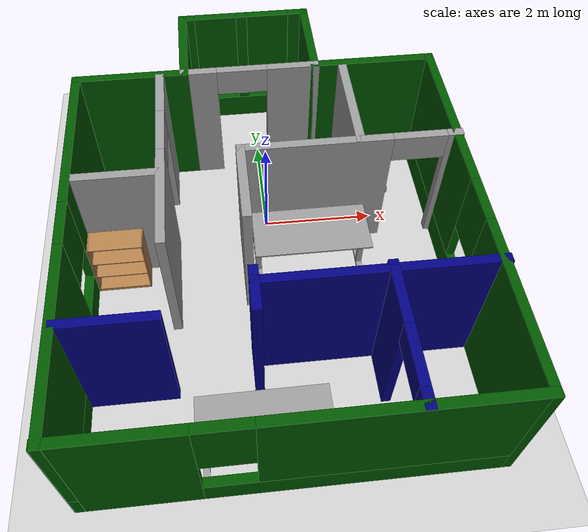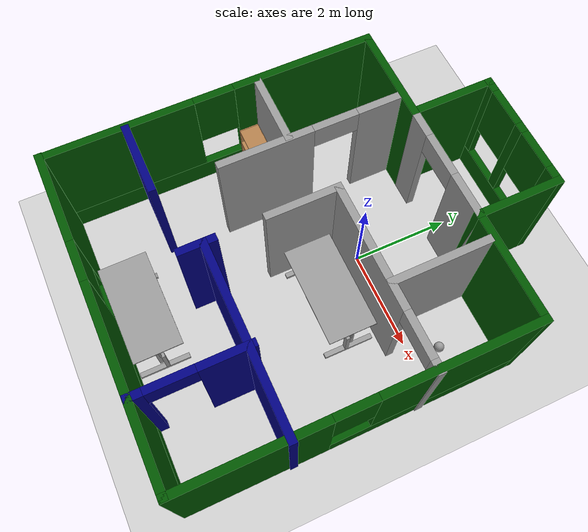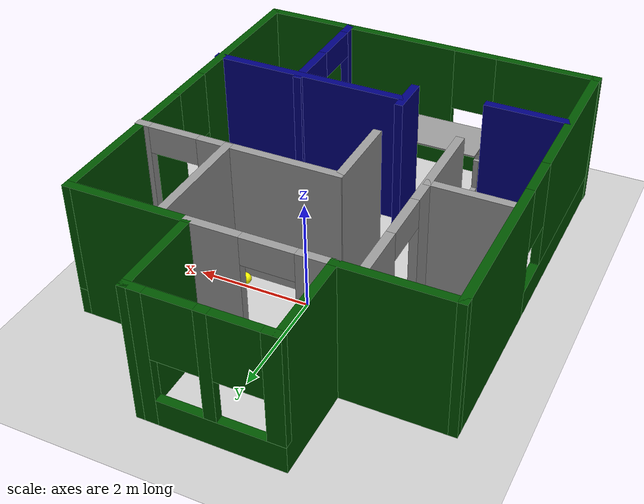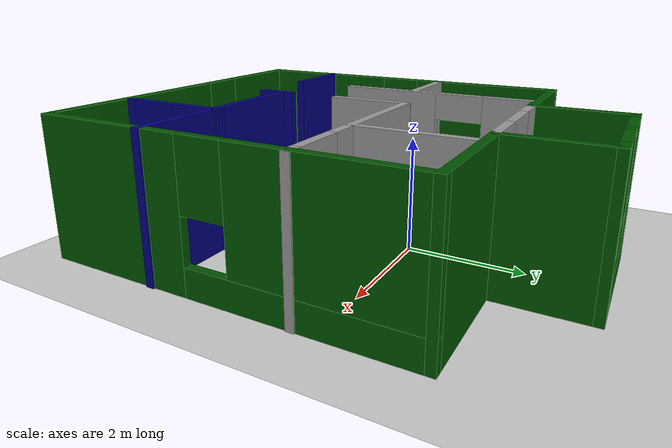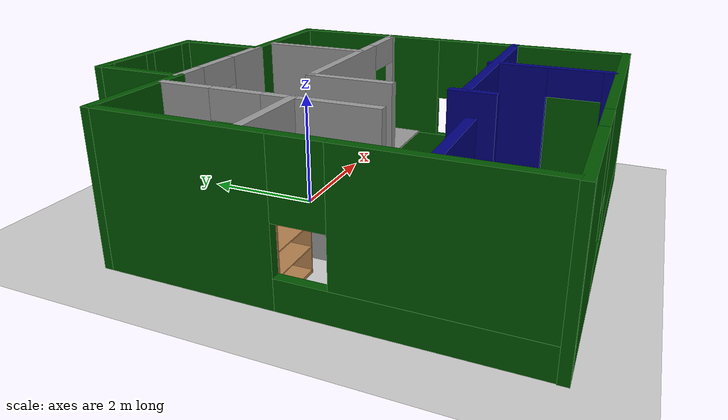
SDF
<sdf version="1.6">
 <world name="default">
  <plugin name="hello" filename="libhello.so"/>
  <light name="sun" type="directional">
   <pose>0 0 10 0 -0 0</pose>
   <diffuse>0.8 0.8 0.8 1</diffuse>
   <specular>0.2 0.2 0.2 1</specular>
   <attenuation>
    <range>1000</range>
    <constant>0.9</constant>
    <linear>0.01</linear>
    <quadratic>0.001</quadratic>
   </attenuation>
   <direction>-0.5 0.1 -0.9</direction>
  </light>
  <model name="ground_plane">
   <static>1</static>
   <link name="link">
    <collision name="collision">
     <geometry><plane><normal>0 0 1</normal><size>100 100</size></plane></geometry>
     <surface>
      <contact><collide_bitmask>65535</collide_bitmask></contact>
      <friction><ode><mu>100</mu><mu2>50</mu2></ode></friction>
     </surface>
    </collision>
    <visual name="visual">
     <cast_shadows>0</cast_shadows>
     <geometry><plane><normal>0 0 1</normal><size>100 100</size></plane></geometry>
     <material>
      <script><uri>file://media/materials/scripts/gazebo.material</uri><name>Gazebo/Grey</name></script>
     </material>
    </visual>
   </link>
  </model>
  <gravity>0 0 -9.8</gravity>
  <magnetic_field>6e-06 2.3e-05 -4.2e-05</magnetic_field>
  <atmosphere type="adiabatic"/>
  <physics name="default_physics" default="0" type="ode">
   <max_step_size>0.001</max_step_size>
   <real_time_factor>1</real_time_factor>
   <real_time_update_rate>1000</real_time_update_rate>
  </physics>
  <scene><ambient>0.4 0.4 0.4 1</ambient><background>0.7 0.7 0.7 1</background><shadows>1</shadows></scene>
  <spherical_coordinates>
   <surface_model>EARTH_WGS84</surface_model>
   <latitude_deg>0</latitude_deg>
   <longitude_deg>0</longitude_deg>
   <elevation>0</elevation>
   <heading_deg>0</heading_deg>
  </spherical_coordinates>
  <model name="desk">
   <link name="link_0">
    <inertial>
     <mass>1</mass>
     <inertia>
      <ixx>0.166667</ixx>
      <ixy>0</ixy>
      <ixz>0</ixz>
      <iyy>0.166667</iyy>
      <iyz>0</iyz>
      <izz>0.166667</izz>
     </inertia>
    </inertial>
    <pose>-0.922434 0.005357 -0.386429 0 -0 0</pose>
    <visual name="visual">
     <geometry><box><size>0.1 1 0.07</size></box></geometry>
     <material>
      <lighting>1</lighting>
      <script><uri>file://media/materials/scripts/gazebo.material</uri><name>Gazebo/Grey</name></script>
      <shader type="pixel"><normal_map>__default__</normal_map></shader>
      <ambient>0.3 0.3 0.3 1</ambient>
      <diffuse>0.7 0.7 0.7 1</diffuse>
      <specular>0.01 0.01 0.01 1</specular>
      <emissive>0 0 0 1</emissive>
     </material>
    </visual>
    <collision name="collision">
     <geometry><box><size>0.1 1 0.07</size></box></geometry>
     <surface>
      <friction>
       <ode><mu>1</mu><mu2>1</mu2><fdir1>0 0 0</fdir1><slip1>0</slip1><slip2>0</slip2></ode>
       <torsional>
        <coefficient>1</coefficient>
        <patch_radius>0</patch_radius>
        <surface_radius>0</surface_radius>
        <use_patch_radius>1</use_patch_radius>
        <ode><slip>0</slip></ode>
       </torsional>
      </friction>
      <bounce><restitution_coefficient>0</restitution_coefficient><threshold>1e+06</threshold></bounce>
      <contact>
       <collide_without_contact>0</collide_without_contact>
       <collide_without_contact_bitmask>1</collide_without_contact_bitmask>
       <collide_bitmask>1</collide_bitmask>
       <ode>
        <soft_cfm>0</soft_cfm>
        <soft_erp>0.2</soft_erp>
        <kp>1e+13</kp>
        <kd>1</kd>
        <max_vel>0.01</max_vel>
        <min_depth>0</min_depth>
       </ode>
       <bullet>
        <split_impulse>1</split_impulse>
        <split_impulse_penetration_threshold>-0.01</split_impulse_penetration_threshold>
        <soft_cfm>0</soft_cfm>
        <soft_erp>0.2</soft_erp>
        <kp>1e+13</kp>
        <kd>1</kd>
       </bullet>
      </contact>
     </surface>
    </collision>
   </link>
   <link name="link_0_clone">
    <inertial>
     <mass>1</mass>
     <inertia>
      <ixx>0.166667</ixx>
      <ixy>0</ixy>
      <ixz>0</ixz>
      <iyy>0.166667</iyy>
      <iyz>0</iyz>
      <izz>0.166667</izz>
     </inertia>
    </inertial>
    <pose>0.913246 0.005357 -0.386429 0 -0 0</pose>
    <visual name="visual">
     <geometry><box><size>0.1 1 0.07</size></box></geometry>
     <material>
      <lighting>1</lighting>
      <script><uri>file://media/materials/scripts/gazebo.material</uri><name>Gazebo/Grey</name></script>
      <shader type="pixel"><normal_map>__default__</normal_map></shader>
      <ambient>0.3 0.3 0.3 1</ambient>
      <diffuse>0.7 0.7 0.7 1</diffuse>
      <specular>0.01 0.01 0.01 1</specular>
      <emissive>0 0 0 1</emissive>
     </material>
    </visual>
    <collision name="collision">
     <geometry><box><size>0.1 1 0.07</size></box></geometry>
     <surface>
      <friction>
       <ode><mu>1</mu><mu2>1</mu2><fdir1>0 0 0</fdir1><slip1>0</slip1><slip2>0</slip2></ode>
       <torsional>
        <coefficient>1</coefficient>
        <patch_radius>0</patch_radius>
        <surface_radius>0</surface_radius>
        <use_patch_radius>1</use_patch_radius>
        <ode><slip>0</slip></ode>
       </torsional>
      </friction>
      <bounce><restitution_coefficient>0</restitution_coefficient><threshold>1e+06</threshold></bounce>
      <contact>
       <collide_without_contact>0</collide_without_contact>
       <collide_without_contact_bitmask>1</collide_without_contact_bitmask>
       <collide_bitmask>1</collide_bitmask>
       <ode>
        <soft_cfm>0</soft_cfm>
        <soft_erp>0.2</soft_erp>
        <kp>1e+13</kp>
        <kd>1</kd>
        <max_vel>0.01</max_vel>
        <min_depth>0</min_depth>
       </ode>
       <bullet>
        <split_impulse>1</split_impulse>
        <split_impulse_penetration_threshold>-0.01</split_impulse_penetration_threshold>
        <soft_cfm>0</soft_cfm>
        <soft_erp>0.2</soft_erp>
        <kp>1e+13</kp>
        <kd>1</kd>
       </bullet>
      </contact>
     </surface>
    </collision>
   </link>
   <link name="link_1">
    <inertial>
     <mass>1</mass>
     <inertia>
      <ixx>0.166667</ixx>
      <ixy>0</ixy>
      <ixz>0</ixz>
      <iyy>0.166667</iyy>
      <iyz>0</iyz>
      <izz>0.166667</izz>
     </inertia>
    </inertial>
    <pose>-0.922434 -0.047143 -0.051429 0 -0 0</pose>
    <visual name="visual">
     <geometry><box><size>0.1 0.07 0.6</size></box></geometry>
     <material>
      <lighting>1</lighting>
      <script><uri>file://media/materials/scripts/gazebo.material</uri><name>Gazebo/Grey</name></script>
      <shader type="pixel"><normal_map>__default__</normal_map></shader>
      <ambient>0.3 0.3 0.3 1</ambient>
      <diffuse>0.7 0.7 0.7 1</diffuse>
      <specular>0.01 0.01 0.01 1</specular>
      <emissive>0 0 0 1</emissive>
     </material>
    </visual>
    <collision name="collision">
     <geometry><box><size>0.1 0.07 0.6</size></box></geometry>
     <surface>
      <friction>
       <ode><mu>1</mu><mu2>1</mu2><fdir1>0 0 0</fdir1><slip1>0</slip1><slip2>0</slip2></ode>
       <torsional>
        <coefficient>1</coefficient>
        <patch_radius>0</patch_radius>
        <surface_radius>0</surface_radius>
        <use_patch_radius>1</use_patch_radius>
        <ode><slip>0</slip></ode>
       </torsional>
      </friction>
      <bounce><restitution_coefficient>0</restitution_coefficient><threshold>1e+06</threshold></bounce>
      <contact>
       <collide_without_contact>0</collide_without_contact>
       <collide_without_contact_bitmask>1</collide_without_contact_bitmask>
       <collide_bitmask>1</collide_bitmask>
       <ode>
        <soft_cfm>0</soft_cfm>
        <soft_erp>0.2</soft_erp>
        <kp>1e+13</kp>
        <kd>1</kd>
        <max_vel>0.01</max_vel>
        <min_depth>0</min_depth>
       </ode>
       <bullet>
        <split_impulse>1</split_impulse>
        <split_impulse_penetration_threshold>-0.01</split_impulse_penetration_threshold>
        <soft_cfm>0</soft_cfm>
        <soft_erp>0.2</soft_erp>
        <kp>1e+13</kp>
        <kd>1</kd>
       </bullet>
      </contact>
     </surface>
    </collision>
   </link>
   <link name="link_1_clone">
    <inertial>
     <mass>1</mass>
     <inertia>
      <ixx>0.166667</ixx>
      <ixy>0</ixy>
      <ixz>0</ixz>
      <iyy>0.166667</iyy>
      <iyz>0</iyz>
      <izz>0.166667</izz>
     </inertia>
    </inertial>
    <pose>-0.922434 0.022857 0.278571 0 -0 0</pose>
    <visual name="visual">
     <geometry><box><size>0.1 0.07 0.6</size></box></geometry>
     <material>
      <lighting>1</lighting>
      <script><uri>file://media/materials/scripts/gazebo.material</uri><name>Gazebo/Grey</name></script>
      <shader type="pixel"><normal_map>__default__</normal_map></shader>
      <ambient>0.3 0.3 0.3 1</ambient>
      <diffuse>0.7 0.7 0.7 1</diffuse>
      <specular>0.01 0.01 0.01 1</specular>
      <emissive>0 0 0 1</emissive>
     </material>
    </visual>
    <collision name="collision">
     <geometry><box><size>0.1 0.07 0.6</size></box></geometry>
     <surface>
      <friction>
       <ode><mu>1</mu><mu2>1</mu2><fdir1>0 0 0</fdir1><slip1>0</slip1><slip2>0</slip2></ode>
       <torsional>
        <coefficient>1</coefficient>
        <patch_radius>0</patch_radius>
        <surface_radius>0</surface_radius>
        <use_patch_radius>1</use_patch_radius>
        <ode><slip>0</slip></ode>
       </torsional>
      </friction>
      <bounce><restitution_coefficient>0</restitution_coefficient><threshold>1e+06</threshold></bounce>
      <contact>
       <collide_without_contact>0</collide_without_contact>
       <collide_without_contact_bitmask>1</collide_without_contact_bitmask>
       <collide_bitmask>1</collide_bitmask>
       <ode>
        <soft_cfm>0</soft_cfm>
        <soft_erp>0.2</soft_erp>
        <kp>1e+13</kp>
        <kd>1</kd>
        <max_vel>0.01</max_vel>
        <min_depth>0</min_depth>
       </ode>
       <bullet>
        <split_impulse>1</split_impulse>
        <split_impulse_penetration_threshold>-0.01</split_impulse_penetration_threshold>
        <soft_cfm>0</soft_cfm>
        <soft_erp>0.2</soft_erp>
        <kp>1e+13</kp>
        <kd>1</kd>
       </bullet>
      </contact>
     </surface>
    </collision>
   </link>
   <link name="link_1_clone_0">
    <inertial>
     <mass>1</mass>
     <inertia>
      <ixx>0.166667</ixx>
      <ixy>0</ixy>
      <ixz>0</ixz>
      <iyy>0.166667</iyy>
      <iyz>0</iyz>
      <izz>0.166667</izz>
     </inertia>
    </inertial>
    <pose>0.913246 -0.047143 -0.051429 0 -0 0</pose>
    <visual name="visual">
     <geometry><box><size>0.1 0.07 0.6</size></box></geometry>
     <material>
      <lighting>1</lighting>
      <script><uri>file://media/materials/scripts/gazebo.material</uri><name>Gazebo/Grey</name></script>
      <shader type="pixel"><normal_map>__default__</normal_map></shader>
      <ambient>0.3 0.3 0.3 1</ambient>
      <diffuse>0.7 0.7 0.7 1</diffuse>
      <specular>0.01 0.01 0.01 1</specular>
      <emissive>0 0 0 1</emissive>
     </material>
    </visual>
    <collision name="collision">
     <geometry><box><size>0.1 0.07 0.6</size></box></geometry>
     <surface>
      <friction>
       <ode><mu>1</mu><mu2>1</mu2><fdir1>0 0 0</fdir1><slip1>0</slip1><slip2>0</slip2></ode>
       <torsional>
        <coefficient>1</coefficient>
        <patch_radius>0</patch_radius>
        <surface_radius>0</surface_radius>
        <use_patch_radius>1</use_patch_radius>
        <ode><slip>0</slip></ode>
       </torsional>
      </friction>
      <bounce><restitution_coefficient>0</restitution_coefficient><threshold>1e+06</threshold></bounce>
      <contact>
       <collide_without_contact>0</collide_without_contact>
       <collide_without_contact_bitmask>1</collide_without_contact_bitmask>
       <collide_bitmask>1</collide_bitmask>
       <ode>
        <soft_cfm>0</soft_cfm>
        <soft_erp>0.2</soft_erp>
        <kp>1e+13</kp>
        <kd>1</kd>
        <max_vel>0.01</max_vel>
        <min_depth>0</min_depth>
       </ode>
       <bullet>
        <split_impulse>1</split_impulse>
        <split_impulse_penetration_threshold>-0.01</split_impulse_penetration_threshold>
        <soft_cfm>0</soft_cfm>
        <soft_erp>0.2</soft_erp>
        <kp>1e+13</kp>
        <kd>1</kd>
       </bullet>
      </contact>
     </surface>
    </collision>
   </link>
   <link name="link_1_clone_clone">
    <inertial>
     <mass>1</mass>
     <inertia>
      <ixx>0.166667</ixx>
      <ixy>0</ixy>
      <ixz>0</ixz>
      <iyy>0.166667</iyy>
      <iyz>0</iyz>
      <izz>0.166667</izz>
     </inertia>
    </inertial>
    <pose>0.913246 0.022857 0.278571 0 -0 0</pose>
    <visual name="visual">
     <geometry><box><size>0.1 0.07 0.6</size></box></geometry>
     <material>
      <lighting>1</lighting>
      <script><uri>file://media/materials/scripts/gazebo.material</uri><name>Gazebo/Grey</name></script>
      <shader type="pixel"><normal_map>__default__</normal_map></shader>
      <ambient>0.3 0.3 0.3 1</ambient>
      <diffuse>0.7 0.7 0.7 1</diffuse>
      <specular>0.01 0.01 0.01 1</specular>
      <emissive>0 0 0 1</emissive>
     </material>
    </visual>
    <collision name="collision">
     <geometry><box><size>0.1 0.07 0.6</size></box></geometry>
     <surface>
      <friction>
       <ode><mu>1</mu><mu2>1</mu2><fdir1>0 0 0</fdir1><slip1>0</slip1><slip2>0</slip2></ode>
       <torsional>
        <coefficient>1</coefficient>
        <patch_radius>0</patch_radius>
        <surface_radius>0</surface_radius>
        <use_patch_radius>1</use_patch_radius>
        <ode><slip>0</slip></ode>
       </torsional>
      </friction>
      <bounce><restitution_coefficient>0</restitution_coefficient><threshold>1e+06</threshold></bounce>
      <contact>
       <collide_without_contact>0</collide_without_contact>
       <collide_without_contact_bitmask>1</collide_without_contact_bitmask>
       <collide_bitmask>1</collide_bitmask>
       <ode>
        <soft_cfm>0</soft_cfm>
        <soft_erp>0.2</soft_erp>
        <kp>1e+13</kp>
        <kd>1</kd>
        <max_vel>0.01</max_vel>
        <min_depth>0</min_depth>
       </ode>
       <bullet>
        <split_impulse>1</split_impulse>
        <split_impulse_penetration_threshold>-0.01</split_impulse_penetration_threshold>
        <soft_cfm>0</soft_cfm>
        <soft_erp>0.2</soft_erp>
        <kp>1e+13</kp>
        <kd>1</kd>
       </bullet>
      </contact>
     </surface>
    </collision>
   </link>
   <link name="link_2">
    <inertial>
     <mass>1</mass>
     <inertia>
      <ixx>0.166667</ixx>
      <ixy>0</ixy>
      <ixz>0</ixz>
      <iyy>0.166667</iyy>
      <iyz>0</iyz>
      <izz>0.166667</izz>
     </inertia>
    </inertial>
    <pose>-0.002434 -0.017143 0.478571 0 -0 0</pose>
    <visual name="visual">
     <geometry><box><size>2 0.03 0.2</size></box></geometry>
     <material>
      <lighting>1</lighting>
      <script><uri>file://media/materials/scripts/gazebo.material</uri><name>Gazebo/Grey</name></script>
      <shader type="pixel"><normal_map>__default__</normal_map></shader>
      <ambient>0.3 0.3 0.3 1</ambient>
      <diffuse>0.7 0.7 0.7 1</diffuse>
      <specular>0.01 0.01 0.01 1</specular>
      <emissive>0 0 0 1</emissive>
     </material>
    </visual>
    <collision name="collision">
     <geometry><box><size>2 0.03 0.2</size></box></geometry>
     <surface>
      <friction>
       <ode><mu>1</mu><mu2>1</mu2><fdir1>0 0 0</fdir1><slip1>0</slip1><slip2>0</slip2></ode>
       <torsional>
        <coefficient>1</coefficient>
        <patch_radius>0</patch_radius>
        <surface_radius>0</surface_radius>
        <use_patch_radius>1</use_patch_radius>
        <ode><slip>0</slip></ode>
       </torsional>
      </friction>
      <bounce><restitution_coefficient>0</restitution_coefficient><threshold>1e+06</threshold></bounce>
      <contact>
       <collide_without_contact>0</collide_without_contact>
       <collide_without_contact_bitmask>1</collide_without_contact_bitmask>
       <collide_bitmask>1</collide_bitmask>
       <ode>
        <soft_cfm>0</soft_cfm>
        <soft_erp>0.2</soft_erp>
        <kp>1e+13</kp>
        <kd>1</kd>
        <max_vel>0.01</max_vel>
        <min_depth>0</min_depth>
       </ode>
       <bullet>
        <split_impulse>1</split_impulse>
        <split_impulse_penetration_threshold>-0.01</split_impulse_penetration_threshold>
        <soft_cfm>0</soft_cfm>
        <soft_erp>0.2</soft_erp>
        <kp>1e+13</kp>
        <kd>1</kd>
       </bullet>
      </contact>
     </surface>
    </collision>
   </link>
   <link name="link_3">
    <inertial>
     <mass>1.59334</mass>
     <inertia>
      <ixx>0.121473</ixx>
      <ixy>0</ixy>
      <ixz>0</ixz>
      <iyy>0.531234</iyy>
      <iyz>0</iyz>
      <izz>0.652468</izz>
     </inertia>
    </inertial>
    <pose>0.001619 -0.000505 0.588571 0 -0 0.006324</pose>
    <visual name="visual">
     <geometry><box><size>2 0.956011 0.03</size></box></geometry>
     <material>
      <lighting>1</lighting>
      <script><uri>file://media/materials/scripts/gazebo.material</uri><name>Gazebo/Grey</name></script>
      <shader type="pixel"><normal_map>__default__</normal_map></shader>
      <ambient>0.3 0.3 0.3 1</ambient>
      <diffuse>0.7 0.7 0.7 1</diffuse>
      <specular>0.01 0.01 0.01 1</specular>
      <emissive>0 0 0 1</emissive>
     </material>
    </visual>
    <collision name="collision">
     <geometry><box><size>2 0.956011 0.03</size></box></geometry>
     <surface>
      <friction>
       <ode><mu>1</mu><mu2>1</mu2><fdir1>0 0 0</fdir1><slip1>0</slip1><slip2>0</slip2></ode>
       <torsional>
        <coefficient>1</coefficient>
        <patch_radius>0</patch_radius>
        <surface_radius>0</surface_radius>
        <use_patch_radius>1</use_patch_radius>
        <ode><slip>0</slip></ode>
       </torsional>
      </friction>
      <bounce><restitution_coefficient>0</restitution_coefficient><threshold>1e+06</threshold></bounce>
      <contact>
       <collide_without_contact>0</collide_without_contact>
       <collide_without_contact_bitmask>1</collide_without_contact_bitmask>
       <collide_bitmask>1</collide_bitmask>
       <ode>
        <soft_cfm>0</soft_cfm>
        <soft_erp>0.2</soft_erp>
        <kp>1e+13</kp>
        <kd>1</kd>
        <max_vel>0.01</max_vel>
        <min_depth>0</min_depth>
       </ode>
       <bullet>
        <split_impulse>1</split_impulse>
        <split_impulse_penetration_threshold>-0.01</split_impulse_penetration_threshold>
        <soft_cfm>0</soft_cfm>
        <soft_erp>0.2</soft_erp>
        <kp>1e+13</kp>
        <kd>1</kd>
       </bullet>
      </contact>
     </surface>
    </collision>
   </link>
   <joint name="link_0_JOINT_0" type="fixed">
    <parent>link_0</parent>
    <child>link_1</child>
    <physics>
     <ode><limit><cfm>0</cfm><erp>0.2</erp></limit><suspension><cfm>0</cfm><erp>0.2</erp></suspension></ode>
    </physics>
   </joint>
   <joint name="link_0_clone_JOINT_2" type="fixed">
    <parent>link_0_clone</parent>
    <child>link_1_clone_0</child>
    <physics>
     <ode><limit><cfm>0</cfm><erp>0.2</erp></limit><suspension><cfm>0</cfm><erp>0.2</erp></suspension></ode>
    </physics>
   </joint>
   <joint name="link_1_clone_JOINT_4" type="fixed">
    <parent>link_1_clone</parent>
    <child>link_2</child>
    <physics>
     <ode><limit><cfm>0</cfm><erp>0.2</erp></limit><suspension><cfm>0</cfm><erp>0.2</erp></suspension></ode>
    </physics>
   </joint>
   <joint name="link_1_clone_clone_JOINT_5" type="fixed">
    <parent>link_1_clone_clone</parent>
    <child>link_2</child>
    <physics>
     <ode><limit><cfm>0</cfm><erp>0.2</erp></limit><suspension><cfm>0</cfm><erp>0.2</erp></suspension></ode>
    </physics>
   </joint>
   <joint name="link_2_JOINT_6" type="fixed">
    <parent>link_2</parent>
    <child>link_3</child>
    <physics>
     <ode><limit><cfm>0</cfm><erp>0.2</erp></limit><suspension><cfm>0</cfm><erp>0.2</erp></suspension></ode>
    </physics>
   </joint>
   <joint name="prismatic_1" type="prismatic">
    <parent>link_1</parent>
    <child>link_1_clone</child>
    <axis>
     <xyz>0 0 1</xyz>
     <use_parent_model_frame>0</use_parent_model_frame>
     <limit><lower>-0.1</lower><upper>0.2</upper><effort>-1</effort><velocity>-1</velocity></limit>
     <dynamics>
      <spring_reference>0</spring_reference>
      <spring_stiffness>0</spring_stiffness>
      <damping>0</damping>
      <friction>0</friction>
     </dynamics>
    </axis>
    <physics>
     <ode><limit><cfm>0</cfm><erp>0.2</erp></limit><suspension><cfm>0</cfm><erp>0.2</erp></suspension></ode>
    </physics>
   </joint>
   <joint name="prismatic_2" type="prismatic">
    <parent>link_1_clone_0</parent>
    <child>link_1_clone_clone</child>
    <axis>
     <xyz>0 0 1</xyz>
     <use_parent_model_frame>0</use_parent_model_frame>
     <limit><lower>-0.1</lower><upper>0.2</upper><effort>-1</effort><velocity>-1</velocity></limit>
     <dynamics>
      <spring_reference>0</spring_reference>
      <spring_stiffness>0</spring_stiffness>
      <damping>0</damping>
      <friction>0</friction>
     </dynamics>
    </axis>
    <physics>
     <ode><limit><cfm>0</cfm><erp>0.2</erp></limit><suspension><cfm>0</cfm><erp>0.2</erp></suspension></ode>
    </physics>
   </joint>
   <static>0</static>
   <pose>0.683537 -1.00333 0.42144 -7e-06 -1.4e-05 -0.00717</pose>
  </model>
  <model name="house">
   <pose>-0.01675 -0.86593 0 0 -0 0</pose>
   <link name="Wall_10">
    <collision name="Wall_10_Collision">
     <geometry><box><size>2.25 0.15 2.5</size></box></geometry>
     <pose>0 0 1.25 0 -0 0</pose>
    </collision>
    <visual name="Wall_10_Visual">
     <pose>0 0 1.25 0 -0 0</pose>
     <geometry><box><size>2.25 0.15 2.5</size></box></geometry>
     <material>
      <script><uri>file://media/materials/scripts/gazebo.material</uri><name>Gazebo/Grey</name></script>
      <ambient>0 0.333333 0 1</ambient>
     </material>
     <meta><layer>0</layer></meta>
    </visual>
    <pose>2.11595 2.48106 0 0 -0 3.14159</pose>
   </link>
   <link name="Wall_11">
    <collision name="Wall_11_Collision">
     <geometry><box><size>1.75 0.15 2.5</size></box></geometry>
     <pose>0 0 1.25 0 -0 0</pose>
    </collision>
    <visual name="Wall_11_Visual">
     <pose>0 0 1.25 0 -0 0</pose>
     <geometry><box><size>1.75 0.15 2.5</size></box></geometry>
     <material>
      <script><uri>file://media/materials/scripts/gazebo.material</uri><name>Gazebo/Grey</name></script>
      <ambient>0 0.333333 0 1</ambient>
     </material>
     <meta><layer>0</layer></meta>
    </visual>
    <pose>1.06595 3.28106 0 0 -0 1.5708</pose>
   </link>
   <link name="Wall_12">
    <pose>-0.10905 4.08106 0 0 -0 3.14159</pose>
    <visual name="Wall_12_Visual_0">
     <pose>-1.05634 0 1.25 0 -0 0</pose>
     <geometry><box><size>0.387325 0.15 2.5</size></box></geometry>
     <material>
      <script><uri>file://media/materials/scripts/gazebo.material</uri><name>Gazebo/Grey</name></script>
      <ambient>0 0.333333 0 1</ambient>
     </material>
     <meta><layer>0</layer></meta>
    </visual>
    <collision name="Wall_12_Collision_0">
     <geometry><box><size>0.387325 0.15 2.5</size></box></geometry>
     <pose>-1.05634 0 1.25 0 -0 0</pose>
    </collision>
    <visual name="Wall_12_Visual_1">
     <pose>0.193662 0 0.25 0 -0 0</pose>
     <geometry><box><size>2.11267 0.15 0.5</size></box></geometry>
     <material>
      <script><uri>file://media/materials/scripts/gazebo.material</uri><name>Gazebo/Grey</name></script>
      <ambient>0 0.333333 0 1</ambient>
     </material>
     <meta><layer>0</layer></meta>
    </visual>
    <collision name="Wall_12_Collision_1">
     <geometry><box><size>2.11267 0.15 0.5</size></box></geometry>
     <pose>0.193662 0 0.25 0 -0 0</pose>
    </collision>
    <visual name="Wall_12_Visual_2">
     <pose>0.041554 0 1.5 0 -0 0</pose>
     <geometry><box><size>0.208458 0.15 2</size></box></geometry>
     <material>
      <script><uri>file://media/materials/scripts/gazebo.material</uri><name>Gazebo/Grey</name></script>
      <ambient>0 0.333333 0 1</ambient>
     </material>
     <meta><layer>0</layer></meta>
    </visual>
    <collision name="Wall_12_Collision_2">
     <geometry><box><size>0.208458 0.15 2</size></box></geometry>
     <pose>0.041554 0 1.5 0 -0 0</pose>
    </collision>
    <visual name="Wall_12_Visual_3">
     <pose>1.09789 0 1.5 0 -0 0</pose>
     <geometry><box><size>0.304217 0.15 2</size></box></geometry>
     <material>
      <script><uri>file://media/materials/scripts/gazebo.material</uri><name>Gazebo/Grey</name></script>
      <ambient>0 0.333333 0 1</ambient>
     </material>
     <meta><layer>0</layer></meta>
    </visual>
    <collision name="Wall_12_Collision_3">
     <geometry><box><size>0.304217 0.15 2</size></box></geometry>
     <pose>1.09789 0 1.5 0 -0 0</pose>
    </collision>
    <visual name="Wall_12_Visual_4">
     <pose>-0.462675 0 1.9 0 -0 0</pose>
     <geometry><box><size>0.8 0.15 1.2</size></box></geometry>
     <material>
      <script><uri>file://media/materials/scripts/gazebo.material</uri><name>Gazebo/Grey</name></script>
      <ambient>0 0.333333 0 1</ambient>
     </material>
     <meta><layer>0</layer></meta>
    </visual>
    <collision name="Wall_12_Collision_4">
     <geometry><box><size>0.8 0.15 1.2</size></box></geometry>
     <pose>-0.462675 0 1.9 0 -0 0</pose>
    </collision>
    <visual name="Wall_12_Visual_5">
     <pose>0.545783 0 1.9 0 -0 0</pose>
     <geometry><box><size>0.8 0.15 1.2</size></box></geometry>
     <material>
      <script><uri>file://media/materials/scripts/gazebo.material</uri><name>Gazebo/Grey</name></script>
      <ambient>0 0.333333 0 1</ambient>
     </material>
     <meta><layer>0</layer></meta>
    </visual>
    <collision name="Wall_12_Collision_5">
     <geometry><box><size>0.8 0.15 1.2</size></box></geometry>
     <pose>0.545783 0 1.9 0 -0 0</pose>
    </collision>
   </link>
   <link name="Wall_13">
    <collision name="Wall_13_Collision">
     <geometry><box><size>1.75 0.15 2.5</size></box></geometry>
     <pose>0 0 1.25 0 -0 0</pose>
    </collision>
    <visual name="Wall_13_Visual">
     <pose>0 0 1.25 0 -0 0</pose>
     <geometry><box><size>1.75 0.15 2.5</size></box></geometry>
     <material>
      <script><uri>file://media/materials/scripts/gazebo.material</uri><name>Gazebo/Grey</name></script>
      <ambient>0 0.333333 0 1</ambient>
     </material>
     <meta><layer>0</layer></meta>
    </visual>
    <pose>-1.28405 3.28106 0 0 -0 -1.5708</pose>
   </link>
   <link name="Wall_14">
    <collision name="Wall_14_Collision">
     <geometry><box><size>2.05 0.15 2.5</size></box></geometry>
     <pose>0 0 1.25 0 -0 0</pose>
    </collision>
    <visual name="Wall_14_Visual">
     <pose>0 0 1.25 0 -0 0</pose>
     <geometry><box><size>2.05 0.15 2.5</size></box></geometry>
     <material>
      <script><uri>file://media/materials/scripts/gazebo.material</uri><name>Gazebo/Grey</name></script>
      <ambient>0 0.333333 0 1</ambient>
     </material>
     <meta><layer>0</layer></meta>
    </visual>
    <pose>-2.23405 2.48106 0 0 -0 3.14159</pose>
   </link>
   <link name="Wall_15">
    <pose>-3.18405 -0.799958 0 0 -0 -1.5708</pose>
    <visual name="Wall_15_Visual_0">
     <pose>-1.90849 0 1.25 0 -0 0</pose>
     <geometry><box><size>2.89522 0.15 2.5</size></box></geometry>
     <material>
      <script><uri>file://media/materials/scripts/gazebo.material</uri><name>Gazebo/Grey</name></script>
      <ambient>0 0.333333 0 1</ambient>
     </material>
     <meta><layer>0</layer></meta>
    </visual>
    <collision name="Wall_15_Collision_0">
     <geometry><box><size>2.89522 0.15 2.5</size></box></geometry>
     <pose>-1.90849 0 1.25 0 -0 0</pose>
    </collision>
    <visual name="Wall_15_Visual_1">
     <pose>1.44761 0 0.25 0 -0 0</pose>
     <geometry><box><size>3.81698 0.15 0.5</size></box></geometry>
     <material>
      <script><uri>file://media/materials/scripts/gazebo.material</uri><name>Gazebo/Grey</name></script>
      <ambient>0 0.333333 0 1</ambient>
     </material>
     <meta><layer>0</layer></meta>
    </visual>
    <collision name="Wall_15_Collision_1">
     <geometry><box><size>3.81698 0.15 0.5</size></box></geometry>
     <pose>1.44761 0 0.25 0 -0 0</pose>
    </collision>
    <visual name="Wall_15_Visual_2">
     <pose>1.84761 0 1.5 0 -0 0</pose>
     <geometry><box><size>3.01699 0.15 2</size></box></geometry>
     <material>
      <script><uri>file://media/materials/scripts/gazebo.material</uri><name>Gazebo/Grey</name></script>
      <ambient>0 0.333333 0 1</ambient>
     </material>
     <meta><layer>0</layer></meta>
    </visual>
    <collision name="Wall_15_Collision_2">
     <geometry><box><size>3.01699 0.15 2</size></box></geometry>
     <pose>1.84761 0 1.5 0 -0 0</pose>
    </collision>
    <visual name="Wall_15_Visual_3">
     <pose>-0.060885 0 1.9 0 -0 0</pose>
     <geometry><box><size>0.8 0.15 1.2</size></box></geometry>
     <material>
      <script><uri>file://media/materials/scripts/gazebo.material</uri><name>Gazebo/Grey</name></script>
      <ambient>0 0.333333 0 1</ambient>
     </material>
     <meta><layer>0</layer></meta>
    </visual>
    <collision name="Wall_15_Collision_3">
     <geometry><box><size>0.8 0.15 1.2</size></box></geometry>
     <pose>-0.060885 0 1.9 0 -0 0</pose>
    </collision>
   </link>
   <link name="Wall_18">
    <pose>-0.10905 2.48106 0 0 -0 0</pose>
    <visual name="Wall_18_Visual_0">
     <pose>-0.923545 0 1.25 0 -0 0</pose>
     <geometry><box><size>0.65291 0.15 2.5</size></box></geometry>
     <material>
      <script><uri>file://media/materials/scripts/gazebo.material</uri><name>Gazebo/Grey</name></script>
      <ambient>1 1 1 1</ambient>
     </material>
     <meta><layer>0</layer></meta>
    </visual>
    <collision name="Wall_18_Collision_0">
     <geometry><box><size>0.65291 0.15 2.5</size></box></geometry>
     <pose>-0.923545 0 1.25 0 -0 0</pose>
    </collision>
    <visual name="Wall_18_Visual_1">
     <pose>0.776455 0 1.25 0 -0 0</pose>
     <geometry><box><size>0.94709 0.15 2.5</size></box></geometry>
     <material>
      <script><uri>file://media/materials/scripts/gazebo.material</uri><name>Gazebo/Grey</name></script>
      <ambient>1 1 1 1</ambient>
     </material>
     <meta><layer>0</layer></meta>
    </visual>
    <collision name="Wall_18_Collision_1">
     <geometry><box><size>0.94709 0.15 2.5</size></box></geometry>
     <pose>0.776455 0 1.25 0 -0 0</pose>
    </collision>
    <visual name="Wall_18_Visual_2">
     <pose>-0.14709 0 2.25 0 -0 0</pose>
     <geometry><box><size>0.9 0.15 0.5</size></box></geometry>
     <material>
      <script><uri>file://media/materials/scripts/gazebo.material</uri><name>Gazebo/Grey</name></script>
      <ambient>1 1 1 1</ambient>
     </material>
     <meta><layer>0</layer></meta>
    </visual>
    <collision name="Wall_18_Collision_2">
     <geometry><box><size>0.9 0.15 0.5</size></box></geometry>
     <pose>-0.14709 0 2.25 0 -0 0</pose>
    </collision>
   </link>
   <link name="Wall_20">
    <pose>1.38768 0.513735 0 0 -0 3.14159</pose>
    <visual name="Wall_20_Visual_0">
     <pose>-1.74188 0 1.25 0 -0 0</pose>
     <geometry><box><size>0.266242 0.15 2.5</size></box></geometry>
     <material>
      <script><uri>file://media/materials/scripts/gazebo.material</uri><name>Gazebo/Grey</name></script>
      <ambient>1 1 1 1</ambient>
     </material>
     <meta><layer>0</layer></meta>
    </visual>
    <collision name="Wall_20_Collision_0">
     <geometry><box><size>0.266242 0.15 2.5</size></box></geometry>
     <pose>-1.74188 0 1.25 0 -0 0</pose>
    </collision>
    <visual name="Wall_20_Visual_1">
     <pose>0.583121 0 1.25 0 -0 0</pose>
     <geometry><box><size>2.58376 0.15 2.5</size></box></geometry>
     <material>
      <script><uri>file://media/materials/scripts/gazebo.material</uri><name>Gazebo/Grey</name></script>
      <ambient>1 1 1 1</ambient>
     </material>
     <meta><layer>0</layer></meta>
    </visual>
    <collision name="Wall_20_Collision_1">
     <geometry><box><size>2.58376 0.15 2.5</size></box></geometry>
     <pose>0.583121 0 1.25 0 -0 0</pose>
    </collision>
    <visual name="Wall_20_Visual_2">
     <pose>-1.15876 0 2.25 0 -0 0</pose>
     <geometry><box><size>0.9 0.15 0.5</size></box></geometry>
     <material>
      <script><uri>file://media/materials/scripts/gazebo.material</uri><name>Gazebo/Grey</name></script>
      <ambient>1 1 1 1</ambient>
     </material>
     <meta><layer>0</layer></meta>
    </visual>
    <collision name="Wall_20_Collision_2">
     <geometry><box><size>0.9 0.15 0.5</size></box></geometry>
     <pose>-1.15876 0 2.25 0 -0 0</pose>
    </collision>
   </link>
   <link name="Wall_21">
    <collision name="Wall_21_Collision">
     <geometry><box><size>1.5 0.15 2.5</size></box></geometry>
     <pose>0 0 1.25 0 -0 0</pose>
    </collision>
    <visual name="Wall_21_Visual">
     <pose>0 0 1.25 0 -0 0</pose>
     <geometry><box><size>1.5 0.15 2.5</size></box></geometry>
     <material>
      <script><uri>file://media/materials/scripts/gazebo.material</uri><name>Gazebo/Grey</name></script>
      <ambient>1 1 1 1</ambient>
     </material>
     <meta><layer>0</layer></meta>
    </visual>
    <pose>-0.42405 -0.161265 0 0 -0 -1.5708</pose>
   </link>
   <link name="Wall_24">
    <collision name="Wall_24_Collision">
     <geometry><box><size>0.75 0.15 2.5</size></box></geometry>
     <pose>0 0 1.25 0 -0 0</pose>
    </collision>
    <visual name="Wall_24_Visual">
     <pose>0 0 1.25 0 -0 0</pose>
     <geometry><box><size>0.75 0.15 2.5</size></box></geometry>
     <material>
      <script><uri>file://media/materials/scripts/gazebo.material</uri><name>Gazebo/Grey</name></script>
      <ambient>0 0 0.498039 1</ambient>
     </material>
     <meta><layer>0</layer></meta>
    </visual>
    <pose>-0.415776 -2.15984 0 0 -0 -1.5708</pose>
   </link>
   <link name="Wall_36">
    <collision name="Wall_36_Collision">
     <geometry><box><size>1.5 0.15 2.5</size></box></geometry>
     <pose>0 0 1.25 0 -0 0</pose>
    </collision>
    <visual name="Wall_36_Visual">
     <pose>0 0 1.25 0 -0 0</pose>
     <geometry><box><size>1.5 0.15 2.5</size></box></geometry>
     <material>
      <script><uri>file://media/materials/scripts/gazebo.material</uri><name>Gazebo/Grey</name></script>
      <ambient>0 0 0.498039 1</ambient>
     </material>
     <meta><layer>0</layer></meta>
    </visual>
    <pose>-2.45376 -2.47368 0 0 -0 0</pose>
   </link>
   <link name="Wall_38">
    <pose>-1.71474 0.603069 0 0 -0 -1.5708</pose>
    <visual name="Wall_38_Visual_0">
     <pose>-1.39969 0 1.25 0 -0 0</pose>
     <geometry><box><size>0.950613 0.15 2.5</size></box></geometry>
     <material>
      <script><uri>file://media/materials/scripts/gazebo.material</uri><name>Gazebo/Grey</name></script>
      <ambient>1 1 1 1</ambient>
     </material>
     <meta><layer>0</layer></meta>
    </visual>
    <collision name="Wall_38_Collision_0">
     <geometry><box><size>0.950613 0.15 2.5</size></box></geometry>
     <pose>-1.39969 0 1.25 0 -0 0</pose>
    </collision>
    <visual name="Wall_38_Visual_1">
     <pose>0.925306 0 1.25 0 -0 0</pose>
     <geometry><box><size>1.89939 0.15 2.5</size></box></geometry>
     <material>
      <script><uri>file://media/materials/scripts/gazebo.material</uri><name>Gazebo/Grey</name></script>
      <ambient>1 1 1 1</ambient>
     </material>
     <meta><layer>0</layer></meta>
    </visual>
    <collision name="Wall_38_Collision_1">
     <geometry><box><size>1.89939 0.15 2.5</size></box></geometry>
     <pose>0.925306 0 1.25 0 -0 0</pose>
    </collision>
    <visual name="Wall_38_Visual_2">
     <pose>-0.474387 0 2.25 0 -0 0</pose>
     <geometry><box><size>0.9 0.15 0.5</size></box></geometry>
     <material>
      <script><uri>file://media/materials/scripts/gazebo.material</uri><name>Gazebo/Grey</name></script>
      <ambient>1 1 1 1</ambient>
     </material>
     <meta><layer>0</layer></meta>
    </visual>
    <collision name="Wall_38_Collision_2">
     <geometry><box><size>0.9 0.15 0.5</size></box></geometry>
     <pose>-0.474387 0 2.25 0 -0 0</pose>
    </collision>
   </link>
   <link name="Wall_40">
    <collision name="Wall_40_Collision">
     <geometry><box><size>1.5 0.15 2.5</size></box></geometry>
     <pose>0 0 1.25 0 -0 0</pose>
    </collision>
    <visual name="Wall_40_Visual">
     <pose>0 0 1.25 0 -0 0</pose>
     <geometry><box><size>1.5 0.15 2.5</size></box></geometry>
     <material>
      <script><uri>file://media/materials/scripts/gazebo.material</uri><name>Gazebo/Grey</name></script>
      <ambient>1 1 1 1</ambient>
     </material>
     <meta><layer>0</layer></meta>
    </visual>
    <pose>-2.41923 0.137532 0 0 -0 0</pose>
   </link>
   <link name="Wall_42">
    <collision name="Wall_42_Collision">
     <geometry><box><size>2 0.15 2.5</size></box></geometry>
     <pose>0 0 1.25 0 -0 0</pose>
    </collision>
    <visual name="Wall_42_Visual">
     <pose>0 0 1.25 0 -0 0</pose>
     <geometry><box><size>2 0.15 2.5</size></box></geometry>
     <material>
      <script><uri>file://media/materials/scripts/gazebo.material</uri><name>Gazebo/Grey</name></script>
      <ambient>1 1 1 1</ambient>
     </material>
     <meta><layer>0</layer></meta>
    </visual>
    <pose>1.55116 1.44868 0 0 -0 -1.5708</pose>
   </link>
   <link name="Wall_44">
    <collision name="Wall_44_Collision">
     <geometry><box><size>3.75 0.15 2.5</size></box></geometry>
     <pose>0 0 1.25 0 -0 0</pose>
    </collision>
    <visual name="Wall_44_Visual">
     <pose>0 0 1.25 0 -0 0</pose>
     <geometry><box><size>3.75 0.15 2.5</size></box></geometry>
     <material>
      <script><uri>file://media/materials/scripts/gazebo.material</uri><name>Gazebo/Grey</name></script>
      <ambient>0 0 0.498039 1</ambient>
     </material>
     <meta><layer>0</layer></meta>
    </visual>
    <pose>1.39578 -2.03829 0 0 -0 3.14159</pose>
   </link>
   <link name="Wall_46">
    <pose>1.56947 -3.02402 0 0 -0 1.5708</pose>
    <visual name="Wall_46_Visual_0">
     <pose>-0.968195 0 1.25 0 -0 0</pose>
     <geometry><box><size>0.313609 0.15 2.5</size></box></geometry>
     <material>
      <script><uri>file://media/materials/scripts/gazebo.material</uri><name>Gazebo/Grey</name></script>
      <ambient>0 0 0.498039 1</ambient>
     </material>
     <meta><layer>0</layer></meta>
    </visual>
    <collision name="Wall_46_Collision_0">
     <geometry><box><size>0.313609 0.15 2.5</size></box></geometry>
     <pose>-0.968195 0 1.25 0 -0 0</pose>
    </collision>
    <visual name="Wall_46_Visual_1">
     <pose>0.606805 0 1.25 0 -0 0</pose>
     <geometry><box><size>1.03639 0.15 2.5</size></box></geometry>
     <material>
      <script><uri>file://media/materials/scripts/gazebo.material</uri><name>Gazebo/Grey</name></script>
      <ambient>0 0 0.498039 1</ambient>
     </material>
     <meta><layer>0</layer></meta>
    </visual>
    <collision name="Wall_46_Collision_1">
     <geometry><box><size>1.03639 0.15 2.5</size></box></geometry>
     <pose>0.606805 0 1.25 0 -0 0</pose>
    </collision>
    <visual name="Wall_46_Visual_2">
     <pose>-0.361391 0 2.25 0 -0 0</pose>
     <geometry><box><size>0.9 0.15 0.5</size></box></geometry>
     <material>
      <script><uri>file://media/materials/scripts/gazebo.material</uri><name>Gazebo/Grey</name></script>
      <ambient>0 0 0.498039 1</ambient>
     </material>
     <meta><layer>0</layer></meta>
    </visual>
    <collision name="Wall_46_Collision_2">
     <geometry><box><size>0.9 0.15 0.5</size></box></geometry>
     <pose>-0.361391 0 2.25 0 -0 0</pose>
    </collision>
   </link>
   <link name="Wall_8">
    <pose>-0.020776 -4.08097 0 0 -0 0</pose>
    <visual name="Wall_8_Visual_0">
     <pose>-2.3025 0 1.25 0 -0 0</pose>
     <geometry><box><size>1.895 0.15 2.5</size></box></geometry>
     <material>
      <script><uri>file://media/materials/scripts/gazebo.material</uri><name>Gazebo/Grey</name></script>
      <ambient>0 0.333333 0 1</ambient>
     </material>
     <meta><layer>0</layer></meta>
    </visual>
    <collision name="Wall_8_Collision_0">
     <geometry><box><size>1.895 0.15 2.5</size></box></geometry>
     <pose>-2.3025 0 1.25 0 -0 0</pose>
    </collision>
    <visual name="Wall_8_Visual_1">
     <pose>0.9475 0 0.25 0 -0 0</pose>
     <geometry><box><size>4.605 0.15 0.5</size></box></geometry>
     <material>
      <script><uri>file://media/materials/scripts/gazebo.material</uri><name>Gazebo/Grey</name></script>
      <ambient>0 0.333333 0 1</ambient>
     </material>
     <meta><layer>0</layer></meta>
    </visual>
    <collision name="Wall_8_Collision_1">
     <geometry><box><size>4.605 0.15 0.5</size></box></geometry>
     <pose>0.9475 0 0.25 0 -0 0</pose>
    </collision>
    <visual name="Wall_8_Visual_2">
     <pose>1.3475 0 1.5 0 -0 0</pose>
     <geometry><box><size>3.805 0.15 2</size></box></geometry>
     <material>
      <script><uri>file://media/materials/scripts/gazebo.material</uri><name>Gazebo/Grey</name></script>
      <ambient>0 0.333333 0 1</ambient>
     </material>
     <meta><layer>0</layer></meta>
    </visual>
    <collision name="Wall_8_Collision_2">
     <geometry><box><size>3.805 0.15 2</size></box></geometry>
     <pose>1.3475 0 1.5 0 -0 0</pose>
    </collision>
    <visual name="Wall_8_Visual_3">
     <pose>-0.955 0 1.9 0 -0 0</pose>
     <geometry><box><size>0.8 0.15 1.2</size></box></geometry>
     <material>
      <script><uri>file://media/materials/scripts/gazebo.material</uri><name>Gazebo/Grey</name></script>
      <ambient>0 0.333333 0 1</ambient>
     </material>
     <meta><layer>0</layer></meta>
    </visual>
    <collision name="Wall_8_Collision_3">
     <geometry><box><size>0.8 0.15 1.2</size></box></geometry>
     <pose>-0.955 0 1.9 0 -0 0</pose>
    </collision>
   </link>
   <link name="Wall_9">
    <pose>3.16595 -0.799958 0 0 -0 1.5708</pose>
    <visual name="Wall_9_Visual_0">
     <pose>-1.94232 0 1.25 0 -0 0</pose>
     <geometry><box><size>2.82757 0.15 2.5</size></box></geometry>
     <material>
      <script><uri>file://media/materials/scripts/gazebo.material</uri><name>Gazebo/Grey</name></script>
      <ambient>0 0.333333 0 1</ambient>
     </material>
     <meta><layer>0</layer></meta>
    </visual>
    <collision name="Wall_9_Collision_0">
     <geometry><box><size>2.82757 0.15 2.5</size></box></geometry>
     <pose>-1.94232 0 1.25 0 -0 0</pose>
    </collision>
    <visual name="Wall_9_Visual_1">
     <pose>1.41378 0 0.25 0 -0 0</pose>
     <geometry><box><size>3.88463 0.15 0.5</size></box></geometry>
     <material>
      <script><uri>file://media/materials/scripts/gazebo.material</uri><name>Gazebo/Grey</name></script>
      <ambient>0 0.333333 0 1</ambient>
     </material>
     <meta><layer>0</layer></meta>
    </visual>
    <collision name="Wall_9_Collision_1">
     <geometry><box><size>3.88463 0.15 0.5</size></box></geometry>
     <pose>1.41378 0 0.25 0 -0 0</pose>
    </collision>
    <visual name="Wall_9_Visual_2">
     <pose>1.81378 0 1.5 0 -0 0</pose>
     <geometry><box><size>3.08464 0.15 2</size></box></geometry>
     <material>
      <script><uri>file://media/materials/scripts/gazebo.material</uri><name>Gazebo/Grey</name></script>
      <ambient>0 0.333333 0 1</ambient>
     </material>
     <meta><layer>0</layer></meta>
    </visual>
    <collision name="Wall_9_Collision_2">
     <geometry><box><size>3.08464 0.15 2</size></box></geometry>
     <pose>1.81378 0 1.5 0 -0 0</pose>
    </collision>
    <visual name="Wall_9_Visual_3">
     <pose>-0.128535 0 1.9 0 -0 0</pose>
     <geometry><box><size>0.8 0.15 1.2</size></box></geometry>
     <material>
      <script><uri>file://media/materials/scripts/gazebo.material</uri><name>Gazebo/Grey</name></script>
      <ambient>0 0.333333 0 1</ambient>
     </material>
     <meta><layer>0</layer></meta>
    </visual>
    <collision name="Wall_9_Collision_3">
     <geometry><box><size>0.8 0.15 1.2</size></box></geometry>
     <pose>-0.128535 0 1.9 0 -0 0</pose>
    </collision>
   </link>
   <static>1</static>
  </model>
  <model name="desk_clone">
   <link name="link_0">
    <inertial>
     <mass>1</mass>
     <inertia>
      <ixx>0.166667</ixx>
      <ixy>0</ixy>
      <ixz>0</ixz>
      <iyy>0.166667</iyy>
      <iyz>0</iyz>
      <izz>0.166667</izz>
     </inertia>
    </inertial>
    <pose>-0.922434 0.005357 -0.386429 0 -0 0</pose>
    <visual name="visual">
     <geometry><box><size>0.1 1 0.07</size></box></geometry>
     <material>
      <lighting>1</lighting>
      <script><uri>file://media/materials/scripts/gazebo.material</uri><name>Gazebo/Grey</name></script>
      <shader type="pixel"><normal_map>__default__</normal_map></shader>
      <ambient>0.3 0.3 0.3 1</ambient>
      <diffuse>0.7 0.7 0.7 1</diffuse>
      <specular>0.01 0.01 0.01 1</specular>
      <emissive>0 0 0 1</emissive>
     </material>
    </visual>
    <collision name="collision">
     <geometry><box><size>0.1 1 0.07</size></box></geometry>
     <surface>
      <friction>
       <ode><mu>1</mu><mu2>1</mu2><fdir1>0 0 0</fdir1><slip1>0</slip1><slip2>0</slip2></ode>
       <torsional>
        <coefficient>1</coefficient>
        <patch_radius>0</patch_radius>
        <surface_radius>0</surface_radius>
        <use_patch_radius>1</use_patch_radius>
        <ode><slip>0</slip></ode>
       </torsional>
      </friction>
      <bounce><restitution_coefficient>0</restitution_coefficient><threshold>1e+06</threshold></bounce>
      <contact>
       <collide_without_contact>0</collide_without_contact>
       <collide_without_contact_bitmask>1</collide_without_contact_bitmask>
       <collide_bitmask>1</collide_bitmask>
       <ode>
        <soft_cfm>0</soft_cfm>
        <soft_erp>0.2</soft_erp>
        <kp>1e+13</kp>
        <kd>1</kd>
        <max_vel>0.01</max_vel>
        <min_depth>0</min_depth>
       </ode>
       <bullet>
        <split_impulse>1</split_impulse>
        <split_impulse_penetration_threshold>-0.01</split_impulse_penetration_threshold>
        <soft_cfm>0</soft_cfm>
        <soft_erp>0.2</soft_erp>
        <kp>1e+13</kp>
        <kd>1</kd>
       </bullet>
      </contact>
     </surface>
    </collision>
   </link>
   <link name="link_0_clone">
    <inertial>
     <mass>1</mass>
     <inertia>
      <ixx>0.166667</ixx>
      <ixy>0</ixy>
      <ixz>0</ixz>
      <iyy>0.166667</iyy>
      <iyz>0</iyz>
      <izz>0.166667</izz>
     </inertia>
    </inertial>
    <pose>0.913246 0.005357 -0.386429 0 -0 0</pose>
    <visual name="visual">
     <geometry><box><size>0.1 1 0.07</size></box></geometry>
     <material>
      <lighting>1</lighting>
      <script><uri>file://media/materials/scripts/gazebo.material</uri><name>Gazebo/Grey</name></script>
      <shader type="pixel"><normal_map>__default__</normal_map></shader>
      <ambient>0.3 0.3 0.3 1</ambient>
      <diffuse>0.7 0.7 0.7 1</diffuse>
      <specular>0.01 0.01 0.01 1</specular>
      <emissive>0 0 0 1</emissive>
     </material>
    </visual>
    <collision name="collision">
     <geometry><box><size>0.1 1 0.07</size></box></geometry>
     <surface>
      <friction>
       <ode><mu>1</mu><mu2>1</mu2><fdir1>0 0 0</fdir1><slip1>0</slip1><slip2>0</slip2></ode>
       <torsional>
        <coefficient>1</coefficient>
        <patch_radius>0</patch_radius>
        <surface_radius>0</surface_radius>
        <use_patch_radius>1</use_patch_radius>
        <ode><slip>0</slip></ode>
       </torsional>
      </friction>
      <bounce><restitution_coefficient>0</restitution_coefficient><threshold>1e+06</threshold></bounce>
      <contact>
       <collide_without_contact>0</collide_without_contact>
       <collide_without_contact_bitmask>1</collide_without_contact_bitmask>
       <collide_bitmask>1</collide_bitmask>
       <ode>
        <soft_cfm>0</soft_cfm>
        <soft_erp>0.2</soft_erp>
        <kp>1e+13</kp>
        <kd>1</kd>
        <max_vel>0.01</max_vel>
        <min_depth>0</min_depth>
       </ode>
       <bullet>
        <split_impulse>1</split_impulse>
        <split_impulse_penetration_threshold>-0.01</split_impulse_penetration_threshold>
        <soft_cfm>0</soft_cfm>
        <soft_erp>0.2</soft_erp>
        <kp>1e+13</kp>
        <kd>1</kd>
       </bullet>
      </contact>
     </surface>
    </collision>
   </link>
   <link name="link_1">
    <inertial>
     <mass>1</mass>
     <inertia>
      <ixx>0.166667</ixx>
      <ixy>0</ixy>
      <ixz>0</ixz>
      <iyy>0.166667</iyy>
      <iyz>0</iyz>
      <izz>0.166667</izz>
     </inertia>
    </inertial>
    <pose>-0.922434 -0.047143 -0.051429 0 -0 0</pose>
    <visual name="visual">
     <geometry><box><size>0.1 0.07 0.6</size></box></geometry>
     <material>
      <lighting>1</lighting>
      <script><uri>file://media/materials/scripts/gazebo.material</uri><name>Gazebo/Grey</name></script>
      <shader type="pixel"><normal_map>__default__</normal_map></shader>
      <ambient>0.3 0.3 0.3 1</ambient>
      <diffuse>0.7 0.7 0.7 1</diffuse>
      <specular>0.01 0.01 0.01 1</specular>
      <emissive>0 0 0 1</emissive>
     </material>
    </visual>
    <collision name="collision">
     <geometry><box><size>0.1 0.07 0.6</size></box></geometry>
     <surface>
      <friction>
       <ode><mu>1</mu><mu2>1</mu2><fdir1>0 0 0</fdir1><slip1>0</slip1><slip2>0</slip2></ode>
       <torsional>
        <coefficient>1</coefficient>
        <patch_radius>0</patch_radius>
        <surface_radius>0</surface_radius>
        <use_patch_radius>1</use_patch_radius>
        <ode><slip>0</slip></ode>
       </torsional>
      </friction>
      <bounce><restitution_coefficient>0</restitution_coefficient><threshold>1e+06</threshold></bounce>
      <contact>
       <collide_without_contact>0</collide_without_contact>
       <collide_without_contact_bitmask>1</collide_without_contact_bitmask>
       <collide_bitmask>1</collide_bitmask>
       <ode>
        <soft_cfm>0</soft_cfm>
        <soft_erp>0.2</soft_erp>
        <kp>1e+13</kp>
        <kd>1</kd>
        <max_vel>0.01</max_vel>
        <min_depth>0</min_depth>
       </ode>
       <bullet>
        <split_impulse>1</split_impulse>
        <split_impulse_penetration_threshold>-0.01</split_impulse_penetration_threshold>
        <soft_cfm>0</soft_cfm>
        <soft_erp>0.2</soft_erp>
        <kp>1e+13</kp>
        <kd>1</kd>
       </bullet>
      </contact>
     </surface>
    </collision>
   </link>
   <link name="link_1_clone">
    <inertial>
     <mass>1</mass>
     <inertia>
      <ixx>0.166667</ixx>
      <ixy>0</ixy>
      <ixz>0</ixz>
      <iyy>0.166667</iyy>
      <iyz>0</iyz>
      <izz>0.166667</izz>
     </inertia>
    </inertial>
    <pose>-0.922434 0.022857 0.278571 0 -0 0</pose>
    <visual name="visual">
     <geometry><box><size>0.1 0.07 0.6</size></box></geometry>
     <material>
      <lighting>1</lighting>
      <script><uri>file://media/materials/scripts/gazebo.material</uri><name>Gazebo/Grey</name></script>
      <shader type="pixel"><normal_map>__default__</normal_map></shader>
      <ambient>0.3 0.3 0.3 1</ambient>
      <diffuse>0.7 0.7 0.7 1</diffuse>
      <specular>0.01 0.01 0.01 1</specular>
      <emissive>0 0 0 1</emissive>
     </material>
    </visual>
    <collision name="collision">
     <geometry><box><size>0.1 0.07 0.6</size></box></geometry>
     <surface>
      <friction>
       <ode><mu>1</mu><mu2>1</mu2><fdir1>0 0 0</fdir1><slip1>0</slip1><slip2>0</slip2></ode>
       <torsional>
        <coefficient>1</coefficient>
        <patch_radius>0</patch_radius>
        <surface_radius>0</surface_radius>
        <use_patch_radius>1</use_patch_radius>
        <ode><slip>0</slip></ode>
       </torsional>
      </friction>
      <bounce><restitution_coefficient>0</restitution_coefficient><threshold>1e+06</threshold></bounce>
      <contact>
       <collide_without_contact>0</collide_without_contact>
       <collide_without_contact_bitmask>1</collide_without_contact_bitmask>
       <collide_bitmask>1</collide_bitmask>
       <ode>
        <soft_cfm>0</soft_cfm>
        <soft_erp>0.2</soft_erp>
        <kp>1e+13</kp>
        <kd>1</kd>
        <max_vel>0.01</max_vel>
        <min_depth>0</min_depth>
       </ode>
       <bullet>
        <split_impulse>1</split_impulse>
        <split_impulse_penetration_threshold>-0.01</split_impulse_penetration_threshold>
        <soft_cfm>0</soft_cfm>
        <soft_erp>0.2</soft_erp>
        <kp>1e+13</kp>
        <kd>1</kd>
       </bullet>
      </contact>
     </surface>
    </collision>
   </link>
   <link name="link_1_clone_0">
    <inertial>
     <mass>1</mass>
     <inertia>
      <ixx>0.166667</ixx>
      <ixy>0</ixy>
      <ixz>0</ixz>
      <iyy>0.166667</iyy>
      <iyz>0</iyz>
      <izz>0.166667</izz>
     </inertia>
    </inertial>
    <pose>0.913246 -0.047143 -0.051429 0 -0 0</pose>
    <visual name="visual">
     <geometry><box><size>0.1 0.07 0.6</size></box></geometry>
     <material>
      <lighting>1</lighting>
      <script><uri>file://media/materials/scripts/gazebo.material</uri><name>Gazebo/Grey</name></script>
      <shader type="pixel"><normal_map>__default__</normal_map></shader>
      <ambient>0.3 0.3 0.3 1</ambient>
      <diffuse>0.7 0.7 0.7 1</diffuse>
      <specular>0.01 0.01 0.01 1</specular>
      <emissive>0 0 0 1</emissive>
     </material>
    </visual>
    <collision name="collision">
     <geometry><box><size>0.1 0.07 0.6</size></box></geometry>
     <surface>
      <friction>
       <ode><mu>1</mu><mu2>1</mu2><fdir1>0 0 0</fdir1><slip1>0</slip1><slip2>0</slip2></ode>
       <torsional>
        <coefficient>1</coefficient>
        <patch_radius>0</patch_radius>
        <surface_radius>0</surface_radius>
        <use_patch_radius>1</use_patch_radius>
        <ode><slip>0</slip></ode>
       </torsional>
      </friction>
      <bounce><restitution_coefficient>0</restitution_coefficient><threshold>1e+06</threshold></bounce>
      <contact>
       <collide_without_contact>0</collide_without_contact>
       <collide_without_contact_bitmask>1</collide_without_contact_bitmask>
       <collide_bitmask>1</collide_bitmask>
       <ode>
        <soft_cfm>0</soft_cfm>
        <soft_erp>0.2</soft_erp>
        <kp>1e+13</kp>
        <kd>1</kd>
        <max_vel>0.01</max_vel>
        <min_depth>0</min_depth>
       </ode>
       <bullet>
        <split_impulse>1</split_impulse>
        <split_impulse_penetration_threshold>-0.01</split_impulse_penetration_threshold>
        <soft_cfm>0</soft_cfm>
        <soft_erp>0.2</soft_erp>
        <kp>1e+13</kp>
        <kd>1</kd>
       </bullet>
      </contact>
     </surface>
    </collision>
   </link>
   <link name="link_1_clone_clone">
    <inertial>
     <mass>1</mass>
     <inertia>
      <ixx>0.166667</ixx>
      <ixy>0</ixy>
      <ixz>0</ixz>
      <iyy>0.166667</iyy>
      <iyz>0</iyz>
      <izz>0.166667</izz>
     </inertia>
    </inertial>
    <pose>0.913246 0.022857 0.278571 0 -0 0</pose>
    <visual name="visual">
     <geometry><box><size>0.1 0.07 0.6</size></box></geometry>
     <material>
      <lighting>1</lighting>
      <script><uri>file://media/materials/scripts/gazebo.material</uri><name>Gazebo/Grey</name></script>
      <shader type="pixel"><normal_map>__default__</normal_map></shader>
      <ambient>0.3 0.3 0.3 1</ambient>
      <diffuse>0.7 0.7 0.7 1</diffuse>
      <specular>0.01 0.01 0.01 1</specular>
      <emissive>0 0 0 1</emissive>
     </material>
    </visual>
    <collision name="collision">
     <geometry><box><size>0.1 0.07 0.6</size></box></geometry>
     <surface>
      <friction>
       <ode><mu>1</mu><mu2>1</mu2><fdir1>0 0 0</fdir1><slip1>0</slip1><slip2>0</slip2></ode>
       <torsional>
        <coefficient>1</coefficient>
        <patch_radius>0</patch_radius>
        <surface_radius>0</surface_radius>
        <use_patch_radius>1</use_patch_radius>
        <ode><slip>0</slip></ode>
       </torsional>
      </friction>
      <bounce><restitution_coefficient>0</restitution_coefficient><threshold>1e+06</threshold></bounce>
      <contact>
       <collide_without_contact>0</collide_without_contact>
       <collide_without_contact_bitmask>1</collide_without_contact_bitmask>
       <collide_bitmask>1</collide_bitmask>
       <ode>
        <soft_cfm>0</soft_cfm>
        <soft_erp>0.2</soft_erp>
        <kp>1e+13</kp>
        <kd>1</kd>
        <max_vel>0.01</max_vel>
        <min_depth>0</min_depth>
       </ode>
       <bullet>
        <split_impulse>1</split_impulse>
        <split_impulse_penetration_threshold>-0.01</split_impulse_penetration_threshold>
        <soft_cfm>0</soft_cfm>
        <soft_erp>0.2</soft_erp>
        <kp>1e+13</kp>
        <kd>1</kd>
       </bullet>
      </contact>
     </surface>
    </collision>
   </link>
   <link name="link_2">
    <inertial>
     <mass>1</mass>
     <inertia>
      <ixx>0.166667</ixx>
      <ixy>0</ixy>
      <ixz>0</ixz>
      <iyy>0.166667</iyy>
      <iyz>0</iyz>
      <izz>0.166667</izz>
     </inertia>
    </inertial>
    <pose>-0.002434 -0.017143 0.478571 0 -0 0</pose>
    <visual name="visual">
     <geometry><box><size>2 0.03 0.2</size></box></geometry>
     <material>
      <lighting>1</lighting>
      <script><uri>file://media/materials/scripts/gazebo.material</uri><name>Gazebo/Grey</name></script>
      <shader type="pixel"><normal_map>__default__</normal_map></shader>
      <ambient>0.3 0.3 0.3 1</ambient>
      <diffuse>0.7 0.7 0.7 1</diffuse>
      <specular>0.01 0.01 0.01 1</specular>
      <emissive>0 0 0 1</emissive>
     </material>
    </visual>
    <collision name="collision">
     <geometry><box><size>2 0.03 0.2</size></box></geometry>
     <surface>
      <friction>
       <ode><mu>1</mu><mu2>1</mu2><fdir1>0 0 0</fdir1><slip1>0</slip1><slip2>0</slip2></ode>
       <torsional>
        <coefficient>1</coefficient>
        <patch_radius>0</patch_radius>
        <surface_radius>0</surface_radius>
        <use_patch_radius>1</use_patch_radius>
        <ode><slip>0</slip></ode>
       </torsional>
      </friction>
      <bounce><restitution_coefficient>0</restitution_coefficient><threshold>1e+06</threshold></bounce>
      <contact>
       <collide_without_contact>0</collide_without_contact>
       <collide_without_contact_bitmask>1</collide_without_contact_bitmask>
       <collide_bitmask>1</collide_bitmask>
       <ode>
        <soft_cfm>0</soft_cfm>
        <soft_erp>0.2</soft_erp>
        <kp>1e+13</kp>
        <kd>1</kd>
        <max_vel>0.01</max_vel>
        <min_depth>0</min_depth>
       </ode>
       <bullet>
        <split_impulse>1</split_impulse>
        <split_impulse_penetration_threshold>-0.01</split_impulse_penetration_threshold>
        <soft_cfm>0</soft_cfm>
        <soft_erp>0.2</soft_erp>
        <kp>1e+13</kp>
        <kd>1</kd>
       </bullet>
      </contact>
     </surface>
    </collision>
   </link>
   <link name="link_3">
    <inertial>
     <mass>1.59334</mass>
     <inertia>
      <ixx>0.121473</ixx>
      <ixy>0</ixy>
      <ixz>0</ixz>
      <iyy>0.531234</iyy>
      <iyz>0</iyz>
      <izz>0.652468</izz>
     </inertia>
    </inertial>
    <pose>0.001619 -0.000505 0.588571 0 -0 0.006324</pose>
    <visual name="visual">
     <geometry><box><size>2 0.956011 0.03</size></box></geometry>
     <material>
      <lighting>1</lighting>
      <script><uri>file://media/materials/scripts/gazebo.material</uri><name>Gazebo/Grey</name></script>
      <shader type="pixel"><normal_map>__default__</normal_map></shader>
      <ambient>0.3 0.3 0.3 1</ambient>
      <diffuse>0.7 0.7 0.7 1</diffuse>
      <specular>0.01 0.01 0.01 1</specular>
      <emissive>0 0 0 1</emissive>
     </material>
    </visual>
    <collision name="collision">
     <geometry><box><size>2 0.956011 0.03</size></box></geometry>
     <surface>
      <friction>
       <ode><mu>1</mu><mu2>1</mu2><fdir1>0 0 0</fdir1><slip1>0</slip1><slip2>0</slip2></ode>
       <torsional>
        <coefficient>1</coefficient>
        <patch_radius>0</patch_radius>
        <surface_radius>0</surface_radius>
        <use_patch_radius>1</use_patch_radius>
        <ode><slip>0</slip></ode>
       </torsional>
      </friction>
      <bounce><restitution_coefficient>0</restitution_coefficient><threshold>1e+06</threshold></bounce>
      <contact>
       <collide_without_contact>0</collide_without_contact>
       <collide_without_contact_bitmask>1</collide_without_contact_bitmask>
       <collide_bitmask>1</collide_bitmask>
       <ode>
        <soft_cfm>0</soft_cfm>
        <soft_erp>0.2</soft_erp>
        <kp>1e+13</kp>
        <kd>1</kd>
        <max_vel>0.01</max_vel>
        <min_depth>0</min_depth>
       </ode>
       <bullet>
        <split_impulse>1</split_impulse>
        <split_impulse_penetration_threshold>-0.01</split_impulse_penetration_threshold>
        <soft_cfm>0</soft_cfm>
        <soft_erp>0.2</soft_erp>
        <kp>1e+13</kp>
        <kd>1</kd>
       </bullet>
      </contact>
     </surface>
    </collision>
   </link>
   <joint name="link_0_JOINT_0" type="fixed">
    <parent>link_0</parent>
    <child>link_1</child>
    <physics>
     <ode><limit><cfm>0</cfm><erp>0.2</erp></limit><suspension><cfm>0</cfm><erp>0.2</erp></suspension></ode>
    </physics>
   </joint>
   <joint name="link_0_clone_JOINT_2" type="fixed">
    <parent>link_0_clone</parent>
    <child>link_1_clone_0</child>
    <physics>
     <ode><limit><cfm>0</cfm><erp>0.2</erp></limit><suspension><cfm>0</cfm><erp>0.2</erp></suspension></ode>
    </physics>
   </joint>
   <joint name="link_1_clone_JOINT_4" type="fixed">
    <parent>link_1_clone</parent>
    <child>link_2</child>
    <physics>
     <ode><limit><cfm>0</cfm><erp>0.2</erp></limit><suspension><cfm>0</cfm><erp>0.2</erp></suspension></ode>
    </physics>
   </joint>
   <joint name="link_1_clone_clone_JOINT_5" type="fixed">
    <parent>link_1_clone_clone</parent>
    <child>link_2</child>
    <physics>
     <ode><limit><cfm>0</cfm><erp>0.2</erp></limit><suspension><cfm>0</cfm><erp>0.2</erp></suspension></ode>
    </physics>
   </joint>
   <joint name="link_2_JOINT_6" type="fixed">
    <parent>link_2</parent>
    <child>link_3</child>
    <physics>
     <ode><limit><cfm>0</cfm><erp>0.2</erp></limit><suspension><cfm>0</cfm><erp>0.2</erp></suspension></ode>
    </physics>
   </joint>
   <joint name="prismatic_1" type="prismatic">
    <parent>link_1</parent>
    <child>link_1_clone</child>
    <axis>
     <xyz>0 0 1</xyz>
     <use_parent_model_frame>0</use_parent_model_frame>
     <limit><lower>-0.1</lower><upper>0.2</upper><effort>-1</effort><velocity>-1</velocity></limit>
     <dynamics>
      <spring_reference>0</spring_reference>
      <spring_stiffness>0</spring_stiffness>
      <damping>0</damping>
      <friction>0</friction>
     </dynamics>
    </axis>
    <physics>
     <ode><limit><cfm>0</cfm><erp>0.2</erp></limit><suspension><cfm>0</cfm><erp>0.2</erp></suspension></ode>
    </physics>
   </joint>
   <joint name="prismatic_2" type="prismatic">
    <parent>link_1_clone_0</parent>
    <child>link_1_clone_clone</child>
    <axis>
     <xyz>0 0 1</xyz>
     <use_parent_model_frame>0</use_parent_model_frame>
     <limit><lower>-0.1</lower><upper>0.2</upper><effort>-1</effort><velocity>-1</velocity></limit>
     <dynamics>
      <spring_reference>0</spring_reference>
      <spring_stiffness>0</spring_stiffness>
      <damping>0</damping>
      <friction>0</friction>
     </dynamics>
    </axis>
    <physics>
     <ode><limit><cfm>0</cfm><erp>0.2</erp></limit><suspension><cfm>0</cfm><erp>0.2</erp></suspension></ode>
    </physics>
   </joint>
   <static>0</static>
   <pose>-0.433559 -4.34783 0.42143 0 -1e-06 3.13996</pose>
  </model>
  <model name="bookshelf">
   <static>1</static>
   <link name="link">
    <inertial><mass>1</mass></inertial>
    <collision name="back">
     <pose>0 0.005 0.6 0 -0 0</pose>
     <geometry><box><size>0.9 0.01 1.2</size></box></geometry>
    </collision>
    <visual name="visual1">
     <pose>0 0.005 0.6 0 -0 0</pose>
     <geometry><box><size>0.9 0.01 1.2</size></box></geometry>
     <material>
      <script><uri>file://media/materials/scripts/gazebo.material</uri><name>Gazebo/Wood</name></script>
     </material>
    </visual>
    <collision name="left_side">
     <pose>0.45 -0.195 0.6 0 -0 0</pose>
     <geometry><box><size>0.02 0.4 1.2</size></box></geometry>
    </collision>
    <visual name="visual2">
     <pose>0.45 -0.195 0.6 0 -0 0</pose>
     <geometry><box><size>0.02 0.4 1.2</size></box></geometry>
     <material>
      <script><uri>file://media/materials/scripts/gazebo.material</uri><name>Gazebo/Wood</name></script>
     </material>
    </visual>
    <collision name="right_side">
     <pose>-0.45 -0.195 0.6 0 -0 0</pose>
     <geometry><box><size>0.02 0.4 1.2</size></box></geometry>
    </collision>
    <visual name="visual3">
     <pose>-0.45 -0.195 0.6 0 -0 0</pose>
     <geometry><box><size>0.02 0.4 1.2</size></box></geometry>
     <material>
      <script><uri>file://media/materials/scripts/gazebo.material</uri><name>Gazebo/Wood</name></script>
     </material>
    </visual>
    <collision name="bottom">
     <pose>0 -0.195 0.03 0 -0 0</pose>
     <geometry><box><size>0.88 0.4 0.06</size></box></geometry>
    </collision>
    <visual name="visual4">
     <pose>0 -0.195 0.03 0 -0 0</pose>
     <geometry><box><size>0.88 0.4 0.06</size></box></geometry>
     <material>
      <script><uri>file://media/materials/scripts/gazebo.material</uri><name>Gazebo/Wood</name></script>
     </material>
    </visual>
    <collision name="top">
     <pose>0 -0.195 1.19 0 -0 0</pose>
     <geometry><box><size>0.88 0.4 0.02</size></box></geometry>
    </collision>
    <visual name="visual5">
     <pose>0 -0.195 1.19 0 -0 0</pose>
     <geometry><box><size>0.88 0.4 0.02</size></box></geometry>
     <material>
      <script><uri>file://media/materials/scripts/gazebo.material</uri><name>Gazebo/Wood</name></script>
     </material>
    </visual>
    <collision name="low_shelf">
     <pose>0 -0.195 0.43 0 -0 0</pose>
     <geometry><box><size>0.88 0.4 0.02</size></box></geometry>
    </collision>
    <visual name="visual6">
     <pose>0 -0.195 0.43 0 -0 0</pose>
     <geometry><box><size>0.88 0.4 0.02</size></box></geometry>
     <material>
      <script><uri>file://media/materials/scripts/gazebo.material</uri><name>Gazebo/Wood</name></script>
     </material>
    </visual>
    <collision name="high_shelf">
     <pose>0 -0.195 0.8 0 -0 0</pose>
     <geometry><box><size>0.88 0.4 0.02</size></box></geometry>
    </collision>
    <visual name="visual7">
     <pose>0 -0.195 0.8 0 -0 0</pose>
     <geometry><box><size>0.88 0.4 0.02</size></box></geometry>
     <material>
      <script><uri>file://media/materials/scripts/gazebo.material</uri><name>Gazebo/Wood</name></script>
     </material>
    </visual>
   </link>
   <pose>-2.65166 -0.817927 0 0 -0 0</pose>
  </model>
  <model name="blue_ball">
   <link name="link_0">
    <inertial>
     <mass>1</mass>
     <inertia><ixx>0.1</ixx><ixy>0</ixy><ixz>0</ixz><iyy>0.1</iyy><iyz>0</iyz><izz>0.1</izz></inertia>
    </inertial>
    <visual name="visual">
     <geometry><sphere><radius>0.1</radius></sphere></geometry>
     <material>
      <lighting>1</lighting>
      <script><uri>file://media/materials/scripts/gazebo.material</uri><name>Gazebo/Grey</name></script>
      <shader type="pixel"><normal_map>__default__</normal_map></shader>
      <ambient>0 0 1 1</ambient>
      <diffuse>0 0 1 1</diffuse>
      <specular>0 0 1 1</specular>
      <emissive>0 0 1 1</emissive>
     </material>
    </visual>
    <collision name="collision">
     <geometry><sphere><radius>0.1</radius></sphere></geometry>
     <surface>
      <friction>
       <ode><mu>1</mu><mu2>1</mu2><fdir1>0 0 0</fdir1><slip1>0</slip1><slip2>0</slip2></ode>
       <torsional>
        <coefficient>1</coefficient>
        <patch_radius>0</patch_radius>
        <surface_radius>0</surface_radius>
        <use_patch_radius>1</use_patch_radius>
        <ode><slip>0</slip></ode>
       </torsional>
      </friction>
      <bounce><restitution_coefficient>0</restitution_coefficient><threshold>1e+06</threshold></bounce>
      <contact>
       <collide_without_contact>0</collide_without_contact>
       <collide_without_contact_bitmask>1</collide_without_contact_bitmask>
       <collide_bitmask>1</collide_bitmask>
       <ode>
        <soft_cfm>0</soft_cfm>
        <soft_erp>0.2</soft_erp>
        <kp>1e+13</kp>
        <kd>1</kd>
        <max_vel>0.01</max_vel>
        <min_depth>0</min_depth>
       </ode>
       <bullet>
        <split_impulse>1</split_impulse>
        <split_impulse_penetration_threshold>-0.01</split_impulse_penetration_threshold>
        <soft_cfm>0</soft_cfm>
        <soft_erp>0.2</soft_erp>
        <kp>1e+13</kp>
        <kd>1</kd>
       </bullet>
      </contact>
     </surface>
    </collision>
   </link>
   <static>0</static>
   <pose>1.18891 0.383605 0.1 0 -0 0</pose>
  </model>
  <model name="green_ball">
   <link name="link_0">
    <inertial>
     <mass>1</mass>
     <inertia><ixx>0.1</ixx><ixy>0</ixy><ixz>0</ixz><iyy>0.1</iyy><iyz>0</iyz><izz>0.1</izz></inertia>
    </inertial>
    <visual name="visual">
     <geometry><sphere><radius>0.1</radius></sphere></geometry>
     <material>
      <lighting>1</lighting>
      <script><uri>file://media/materials/scripts/gazebo.material</uri><name>Gazebo/Grey</name></script>
      <shader type="pixel"><normal_map>__default__</normal_map></shader>
      <ambient>0.12 0.76 0.46 1</ambient>
      <diffuse>0.12 0.76 0.46 1</diffuse>
      <specular>0.12 0.76 0.46 1</specular>
      <emissive>0.12 0.76 0.46 1</emissive>
     </material>
    </visual>
    <collision name="collision">
     <geometry><sphere><radius>0.1</radius></sphere></geometry>
     <surface>
      <friction>
       <ode><mu>1</mu><mu2>1</mu2><fdir1>0 0 0</fdir1><slip1>0</slip1><slip2>0</slip2></ode>
       <torsional>
        <coefficient>1</coefficient>
        <patch_radius>0</patch_radius>
        <surface_radius>0</surface_radius>
        <use_patch_radius>1</use_patch_radius>
        <ode><slip>0</slip></ode>
       </torsional>
      </friction>
      <bounce><restitution_coefficient>0</restitution_coefficient><threshold>1e+06</threshold></bounce>
      <contact>
       <collide_without_contact>0</collide_without_contact>
       <collide_without_contact_bitmask>1</collide_without_contact_bitmask>
       <collide_bitmask>1</collide_bitmask>
       <ode>
        <soft_cfm>0</soft_cfm>
        <soft_erp>0.2</soft_erp>
        <kp>1e+13</kp>
        <kd>1</kd>
        <max_vel>0.01</max_vel>
        <min_depth>0</min_depth>
       </ode>
       <bullet>
        <split_impulse>1</split_impulse>
        <split_impulse_penetration_threshold>-0.01</split_impulse_penetration_threshold>
        <soft_cfm>0</soft_cfm>
        <soft_erp>0.2</soft_erp>
        <kp>1e+13</kp>
        <kd>1</kd>
       </bullet>
      </contact>
     </surface>
    </collision>
   </link>
   <static>0</static>
   <pose>1.20207 0.844553 0.1 0 -0 0</pose>
  </model>
  <model name="yellow_ball">
   <link name="link_0">
    <inertial>
     <mass>1</mass>
     <inertia><ixx>0.1</ixx><ixy>0</ixy><ixz>0</ixz><iyy>0.1</iyy><iyz>0</iyz><izz>0.1</izz></inertia>
    </inertial>
    <visual name="visual">
     <geometry><sphere><radius>0.1</radius></sphere></geometry>
     <material>
      <lighting>1</lighting>
      <script><uri>file://media/materials/scripts/gazebo.material</uri><name>Gazebo/Grey</name></script>
      <shader type="pixel"><normal_map>__default__</normal_map></shader>
      <ambient>1 1 0 1</ambient>
      <diffuse>1 1 0 1</diffuse>
      <specular>1 1 0 1</specular>
      <emissive>1 1 0 1</emissive>
     </material>
    </visual>
    <collision name="collision">
     <geometry><sphere><radius>0.1</radius></sphere></geometry>
     <surface>
      <friction>
       <ode><mu>1</mu><mu2>1</mu2><fdir1>0 0 0</fdir1><slip1>0</slip1><slip2>0</slip2></ode>
       <torsional>
        <coefficient>1</coefficient>
        <patch_radius>0</patch_radius>
        <surface_radius>0</surface_radius>
        <use_patch_radius>1</use_patch_radius>
        <ode><slip>0</slip></ode>
       </torsional>
      </friction>
      <bounce><restitution_coefficient>0</restitution_coefficient><threshold>1e+06</threshold></bounce>
      <contact>
       <collide_without_contact>0</collide_without_contact>
       <collide_without_contact_bitmask>1</collide_without_contact_bitmask>
       <collide_bitmask>1</collide_bitmask>
       <ode>
        <soft_cfm>0</soft_cfm>
        <soft_erp>0.2</soft_erp>
        <kp>1e+13</kp>
        <kd>1</kd>
        <max_vel>0.01</max_vel>
        <min_depth>0</min_depth>
       </ode>
       <bullet>
        <split_impulse>1</split_impulse>
        <split_impulse_penetration_threshold>-0.01</split_impulse_penetration_threshold>
        <soft_cfm>0</soft_cfm>
        <soft_erp>0.2</soft_erp>
        <kp>1e+13</kp>
        <kd>1</kd>
       </bullet>
      </contact>
     </surface>
    </collision>
   </link>
   <static>0</static>
   <pose>1.19328 -0.069316 0.1 0 -0 0</pose>
  </model>
  <model name="white_ball">
   <link name="link_0">
    <inertial>
     <mass>1</mass>
     <inertia><ixx>0.1</ixx><ixy>0</ixy><ixz>0</ixz><iyy>0.1</iyy><iyz>0</iyz><izz>0.1</izz></inertia>
    </inertial>
    <visual name="visual">
     <geometry><sphere><radius>0.1</radius></sphere></geometry>
     <material>
      <lighting>1</lighting>
      <script><uri>file://media/materials/scripts/gazebo.material</uri><name>Gazebo/Grey</name></script>
      <shader type="pixel"><normal_map>__default__</normal_map></shader>
      <ambient>1 1 1 1</ambient>
      <diffuse>1 1 1 1</diffuse>
      <specular>1 1 1 1</specular>
      <emissive>1 1 1 1</emissive>
     </material>
    </visual>
    <collision name="collision">
     <geometry><sphere><radius>0.1</radius></sphere></geometry>
     <surface>
      <friction>
       <ode><mu>1</mu><mu2>1</mu2><fdir1>0 0 0</fdir1><slip1>0</slip1><slip2>0</slip2></ode>
       <torsional>
        <coefficient>1</coefficient>
        <patch_radius>0</patch_radius>
        <surface_radius>0</surface_radius>
        <use_patch_radius>1</use_patch_radius>
        <ode><slip>0</slip></ode>
       </torsional>
      </friction>
      <bounce><restitution_coefficient>0</restitution_coefficient><threshold>1e+06</threshold></bounce>
      <contact>
       <collide_without_contact>0</collide_without_contact>
       <collide_without_contact_bitmask>1</collide_without_contact_bitmask>
       <collide_bitmask>1</collide_bitmask>
       <ode>
        <soft_cfm>0</soft_cfm>
        <soft_erp>0.2</soft_erp>
        <kp>1e+13</kp>
        <kd>1</kd>
        <max_vel>0.01</max_vel>
        <min_depth>0</min_depth>
       </ode>
       <bullet>
        <split_impulse>1</split_impulse>
        <split_impulse_penetration_threshold>-0.01</split_impulse_penetration_threshold>
        <soft_cfm>0</soft_cfm>
        <soft_erp>0.2</soft_erp>
        <kp>1e+13</kp>
        <kd>1</kd>
       </bullet>
      </contact>
     </surface>
    </collision>
   </link>
   <static>0</static>
   <pose>2.36671 0.574948 0.1 0 -0 0</pose>
  </model>
  <model name="red_ball">
   <link name="link_0">
    <inertial>
     <mass>1</mass>
     <inertia><ixx>0.1</ixx><ixy>0</ixy><ixz>0</ixz><iyy>0.1</iyy><iyz>0</iyz><izz>0.1</izz></inertia>
    </inertial>
    <visual name="visual">
     <geometry><sphere><radius>0.1</radius></sphere></geometry>
     <material>
      <lighting>1</lighting>
      <script><uri>file://media/materials/scripts/gazebo.material</uri><name>Gazebo/Grey</name></script>
      <shader type="pixel"><normal_map>__default__</normal_map></shader>
      <ambient>1 0 0 1</ambient>
      <diffuse>1 0 0 1</diffuse>
      <specular>1 0 0 1</specular>
      <emissive>1 0 0 1</emissive>
     </material>
    </visual>
    <collision name="collision">
     <geometry><sphere><radius>0.1</radius></sphere></geometry>
     <surface>
      <friction>
       <ode><mu>1</mu><mu2>1</mu2><fdir1>0 0 0</fdir1><slip1>0</slip1><slip2>0</slip2></ode>
       <torsional>
        <coefficient>1</coefficient>
        <patch_radius>0</patch_radius>
        <surface_radius>0</surface_radius>
        <use_patch_radius>1</use_patch_radius>
        <ode><slip>0</slip></ode>
       </torsional>
      </friction>
      <bounce><restitution_coefficient>0</restitution_coefficient><threshold>1e+06</threshold></bounce>
      <contact>
       <collide_without_contact>0</collide_without_contact>
       <collide_without_contact_bitmask>1</collide_without_contact_bitmask>
       <collide_bitmask>1</collide_bitmask>
       <ode>
        <soft_cfm>0</soft_cfm>
        <soft_erp>0.2</soft_erp>
        <kp>1e+13</kp>
        <kd>1</kd>
        <max_vel>0.01</max_vel>
        <min_depth>0</min_depth>
       </ode>
       <bullet>
        <split_impulse>1</split_impulse>
        <split_impulse_penetration_threshold>-0.01</split_impulse_penetration_threshold>
        <soft_cfm>0</soft_cfm>
        <soft_erp>0.2</soft_erp>
        <kp>1e+13</kp>
        <kd>1</kd>
       </bullet>
      </contact>
     </surface>
    </collision>
   </link>
   <static>0</static>
   <pose>1.20233 1.27496 0.1 0 -0 0</pose>
  </model>
 </world>
</sdf>
